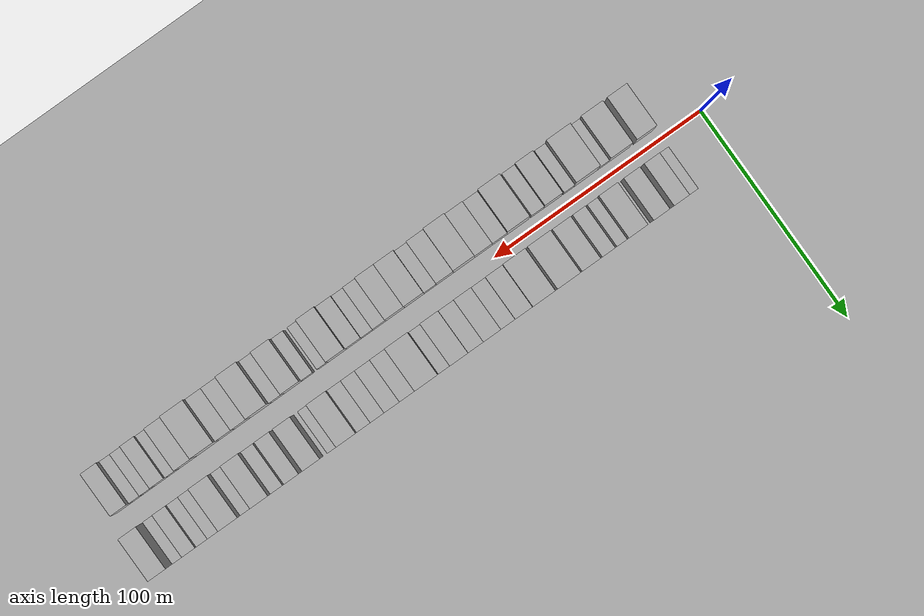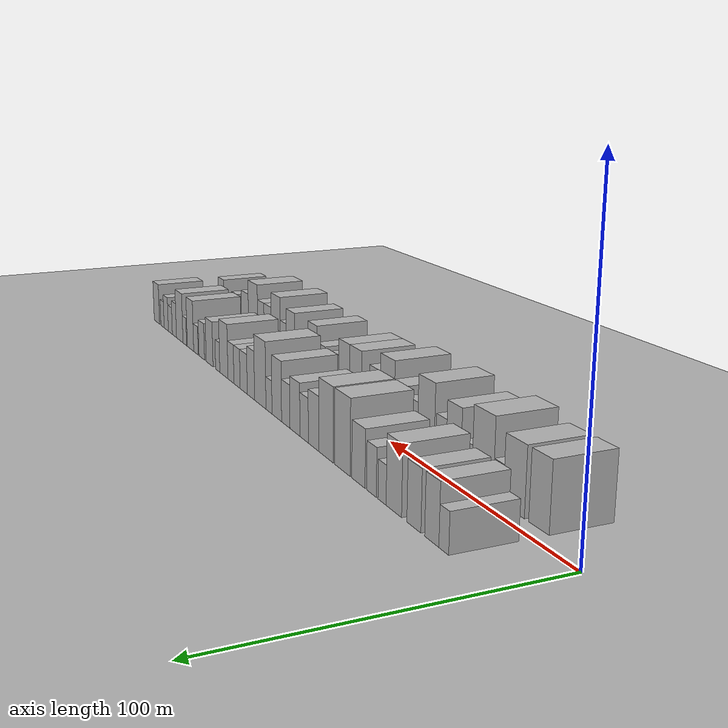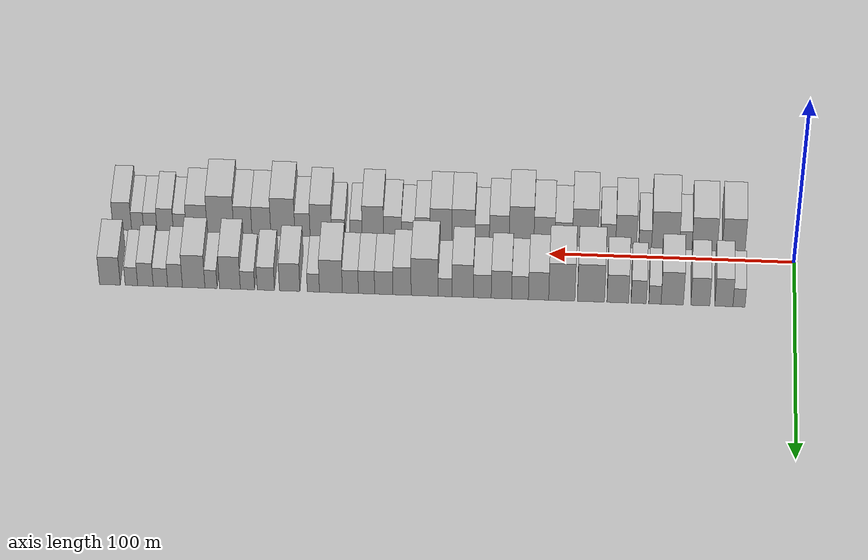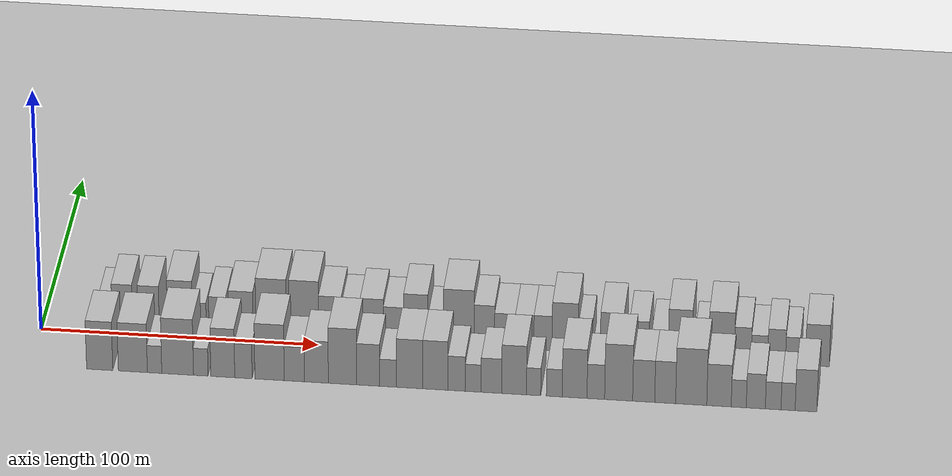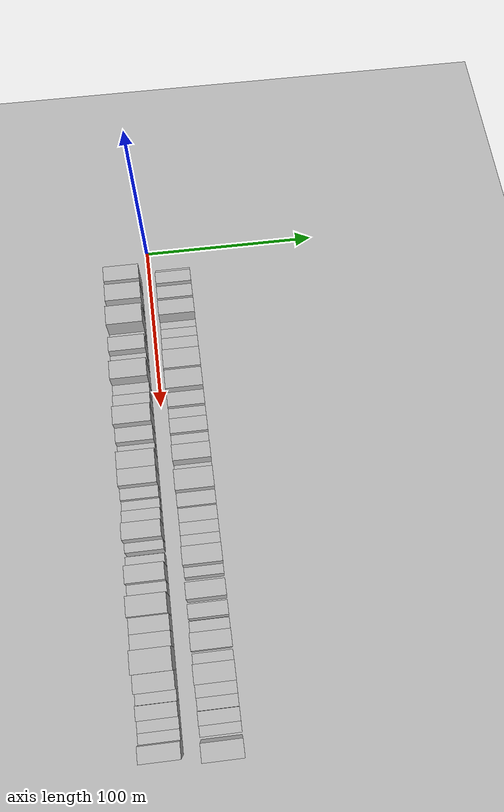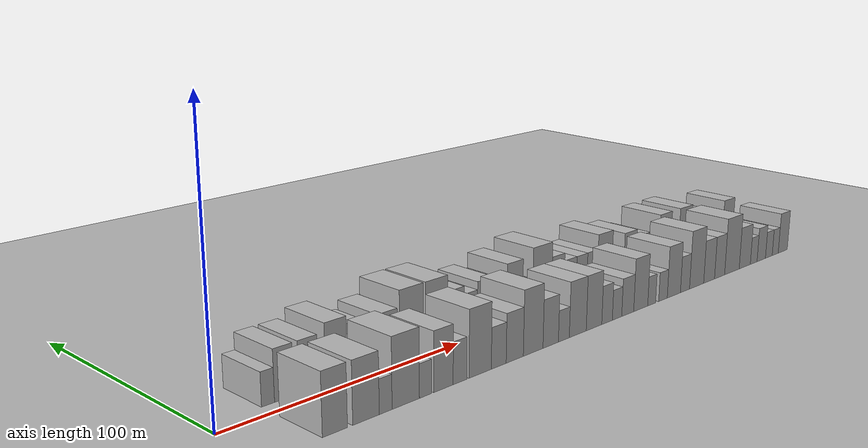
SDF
<?xml version="1.0" encoding="utf-8"?>

<sdf version="1.6">

   <world name="default">

      <gui fullscreen="0">

         <camera name="user_camera">

            <pose>-15 0 4.57585 0 0 0</pose>

            <view_controller>orbit</view_controller>

         </camera>

      </gui>

      <scene>

         <sky>

           <clouds>

             <speed>12</speed>

           </clouds>

         </sky>

         <ambient>0.4 0.4 0.4 1</ambient>

         <background>0.7 0.7 0.7 1</background>

         <shadows>1</shadows>

      </scene>

      <gravity>0 0 -9.8066</gravity>

      <magnetic_field>6e-06 2.3e-05 -4.2e-05</magnetic_field>

      <physics default="0" name="default_physics" type="ode">

         <ode>

            <solver>

               <type>quick</type>

               <iters>10</iters>

               <sor>1.0</sor>

               <use_dynamic_moi_rescaling>0</use_dynamic_moi_rescaling>

            </solver>

            <constraints>

               <cfm>0</cfm>

               <erp>0.2</erp>

               <contact_max_correcting_vel>100</contact_max_correcting_vel>

               <contact_surface_layer>0.001</contact_surface_layer>

            </constraints>

         </ode>

         <max_step_size>0.004</max_step_size>

         <real_time_factor>1</real_time_factor>

         <real_time_update_rate>250</real_time_update_rate>

      </physics>

      <light name="sun" type="directional">

         <cast_shadows>1</cast_shadows>

         <pose>0 0 10 0 0 0</pose>

         <diffuse>0.8 0.8 0.8 1</diffuse>

         <specular>0.2 0.2 0.2 1</specular>

         <attenuation>

            <range>1000</range>

            <constant>0.9</constant>

            <linear>0.01</linear>

            <quadratic>0.001</quadratic>

         </attenuation>

         <direction>-0.5 0.1 -0.9</direction>

      </light>

      <include>

         <name>ground_plane_1</name>

         <uri>model://HANNAS_ground_plane</uri>

         <pose>0 0 0  0 0 0</pose>

      </include>

      <include>

         <name>ground_plane_2</name>

         <uri>model://HANNAS_ground_plane</uri>

         <pose>100 0 0  0 0 0</pose>

      </include>

      <model name="building_1">

         <static>1</static>

         <pose frame="">22.4527 14.5000 0 0.000000 0.000000 1.570796</pose>

         <link name="link">

            <pose frame="">0 0 6.00 0 0 0</pose>

            <collision name="collision">

               <geometry>

                  <box>

                     <size>20.0000 4.9055 12.0000</size>

                  </box>

               </geometry>

               <max_contacts>10</max_contacts>

               <surface>

                  <contact>

                     <ode/>

                  </contact>

                  <bounce/>

                  <friction>

                     <torsional>

                        <ode/>

                     </torsional>

                     <ode/>

                  </friction>

               </surface>

            </collision>

            <visual name="visual">

               <cast_shadows>0</cast_shadows>

               <geometry>

                  <box>

                     <size>20.0000 4.9055 12.0000</size>

                  </box>

               </geometry>

               <material>

                  <script>

                     <uri>model://HANNAS_wall/materials/scripts</uri>

                     <uri>model://HANNAS_wall/materials/textures</uri>

                     <name>vrc/HANNAS_wall</name>

                  </script>

               </material>

            </visual>

            <self_collide>0</self_collide>

            <enable_wind>0</enable_wind>

            <kinematic>0</kinematic>

         </link>

      </model>

      <model name="building_2">

         <static>1</static>

         <pose frame="">28.5818 14.5000 0 0.000000 0.000000 1.570796</pose>

         <link name="link">

            <pose frame="">0 0 9.00 0 0 0</pose>

            <collision name="collision">

               <geometry>

                  <box>

                     <size>20.0000 7.3527 18.0000</size>

                  </box>

               </geometry>

               <max_contacts>10</max_contacts>

               <surface>

                  <contact>

                     <ode/>

                  </contact>

                  <bounce/>

                  <friction>

                     <torsional>

                        <ode/>

                     </torsional>

                     <ode/>

                  </friction>

               </surface>

            </collision>

            <visual name="visual">

               <cast_shadows>0</cast_shadows>

               <geometry>

                  <box>

                     <size>20.0000 7.3527 18.0000</size>

                  </box>

               </geometry>

               <material>

                  <script>

                     <uri>model://HANNAS_wall/materials/scripts</uri>

                     <uri>model://HANNAS_wall/materials/textures</uri>

                     <name>vrc/HANNAS_wall</name>

                  </script>

               </material>

            </visual>

            <self_collide>0</self_collide>

            <enable_wind>0</enable_wind>

            <kinematic>0</kinematic>

         </link>

      </model>

      <model name="building_3">

         <static>1</static>

         <pose frame="">38.1045 14.5000 0 0.000000 0.000000 1.570796</pose>

         <link name="link">

            <pose frame="">0 0 9.00 0 0 0</pose>

            <collision name="collision">

               <geometry>

                  <box>

                     <size>20.0000 7.6926 18.0000</size>

                  </box>

               </geometry>

               <max_contacts>10</max_contacts>

               <surface>

                  <contact>

                     <ode/>

                  </contact>

                  <bounce/>

                  <friction>

                     <torsional>

                        <ode/>

                     </torsional>

                     <ode/>

                  </friction>

               </surface>

            </collision>

            <visual name="visual">

               <cast_shadows>0</cast_shadows>

               <geometry>

                  <box>

                     <size>20.0000 7.6926 18.0000</size>

                  </box>

               </geometry>

               <material>

                  <script>

                     <uri>model://HANNAS_wall/materials/scripts</uri>

                     <uri>model://HANNAS_wall/materials/textures</uri>

                     <name>vrc/HANNAS_wall</name>

                  </script>

               </material>

            </visual>

            <self_collide>0</self_collide>

            <enable_wind>0</enable_wind>

            <kinematic>0</kinematic>

         </link>

      </model>

      <model name="building_4">

         <static>1</static>

         <pose frame="">49.4682 14.5000 0 0.000000 0.000000 1.570796</pose>

         <link name="link">

            <pose frame="">0 0 10.50 0 0 0</pose>

            <collision name="collision">

               <geometry>

                  <box>

                     <size>20.0000 9.0349 21.0000</size>

                  </box>

               </geometry>

               <max_contacts>10</max_contacts>

               <surface>

                  <contact>

                     <ode/>

                  </contact>

                  <bounce/>

                  <friction>

                     <torsional>

                        <ode/>

                     </torsional>

                     <ode/>

                  </friction>

               </surface>

            </collision>

            <visual name="visual">

               <cast_shadows>0</cast_shadows>

               <geometry>

                  <box>

                     <size>20.0000 9.0349 21.0000</size>

                  </box>

               </geometry>

               <material>

                  <script>

                     <uri>model://HANNAS_wall/materials/scripts</uri>

                     <uri>model://HANNAS_wall/materials/textures</uri>

                     <name>vrc/HANNAS_wall</name>

                  </script>

               </material>

            </visual>

            <self_collide>0</self_collide>

            <enable_wind>0</enable_wind>

            <kinematic>0</kinematic>

         </link>

      </model>

      <model name="building_5">

         <static>1</static>

         <pose frame="">56.4635 14.5000 0 0.000000 0.000000 1.570796</pose>

         <link name="link">

            <pose frame="">0 0 6.00 0 0 0</pose>

            <collision name="collision">

               <geometry>

                  <box>

                     <size>20.0000 4.9556 12.0000</size>

                  </box>

               </geometry>

               <max_contacts>10</max_contacts>

               <surface>

                  <contact>

                     <ode/>

                  </contact>

                  <bounce/>

                  <friction>

                     <torsional>

                        <ode/>

                     </torsional>

                     <ode/>

                  </friction>

               </surface>

            </collision>

            <visual name="visual">

               <cast_shadows>0</cast_shadows>

               <geometry>

                  <box>

                     <size>20.0000 4.9556 12.0000</size>

                  </box>

               </geometry>

               <material>

                  <script>

                     <uri>model://HANNAS_wall/materials/scripts</uri>

                     <uri>model://HANNAS_wall/materials/textures</uri>

                     <name>vrc/HANNAS_wall</name>

                  </script>

               </material>

            </visual>

            <self_collide>0</self_collide>

            <enable_wind>0</enable_wind>

            <kinematic>0</kinematic>

         </link>

      </model>

      <model name="building_6">

         <static>1</static>

         <pose frame="">63.0217 14.5000 0 0.000000 0.000000 1.570796</pose>

         <link name="link">

            <pose frame="">0 0 7.50 0 0 0</pose>

            <collision name="collision">

               <geometry>

                  <box>

                     <size>20.0000 6.1607 15.0000</size>

                  </box>

               </geometry>

               <max_contacts>10</max_contacts>

               <surface>

                  <contact>

                     <ode/>

                  </contact>

                  <bounce/>

                  <friction>

                     <torsional>

                        <ode/>

                     </torsional>

                     <ode/>

                  </friction>

               </surface>

            </collision>

            <visual name="visual">

               <cast_shadows>0</cast_shadows>

               <geometry>

                  <box>

                     <size>20.0000 6.1607 15.0000</size>

                  </box>

               </geometry>

               <material>

                  <script>

                     <uri>model://HANNAS_wall/materials/scripts</uri>

                     <uri>model://HANNAS_wall/materials/textures</uri>

                     <name>vrc/HANNAS_wall</name>

                  </script>

               </material>

            </visual>

            <self_collide>0</self_collide>

            <enable_wind>0</enable_wind>

            <kinematic>0</kinematic>

         </link>

      </model>

      <model name="building_7">

         <static>1</static>

         <pose frame="">71.4967 14.5000 0 0.000000 0.000000 1.570796</pose>

         <link name="link">

            <pose frame="">0 0 9.00 0 0 0</pose>

            <collision name="collision">

               <geometry>

                  <box>

                     <size>20.0000 8.7894 18.0000</size>

                  </box>

               </geometry>

               <max_contacts>10</max_contacts>

               <surface>

                  <contact>

                     <ode/>

                  </contact>

                  <bounce/>

                  <friction>

                     <torsional>

                        <ode/>

                     </torsional>

                     <ode/>

                  </friction>

               </surface>

            </collision>

            <visual name="visual">

               <cast_shadows>0</cast_shadows>

               <geometry>

                  <box>

                     <size>20.0000 8.7894 18.0000</size>

                  </box>

               </geometry>

               <material>

                  <script>

                     <uri>model://HANNAS_wall/materials/scripts</uri>

                     <uri>model://HANNAS_wall/materials/textures</uri>

                     <name>vrc/HANNAS_wall</name>

                  </script>

               </material>

            </visual>

            <self_collide>0</self_collide>

            <enable_wind>0</enable_wind>

            <kinematic>0</kinematic>

         </link>

      </model>

      <model name="building_8">

         <static>1</static>

         <pose frame="">82.3796 14.5000 0 0.000000 0.000000 1.570796</pose>

         <link name="link">

            <pose frame="">0 0 12.00 0 0 0</pose>

            <collision name="collision">

               <geometry>

                  <box>

                     <size>20.0000 10.9763 24.0000</size>

                  </box>

               </geometry>

               <max_contacts>10</max_contacts>

               <surface>

                  <contact>

                     <ode/>

                  </contact>

                  <bounce/>

                  <friction>

                     <torsional>

                        <ode/>

                     </torsional>

                     <ode/>

                  </friction>

               </surface>

            </collision>

            <visual name="visual">

               <cast_shadows>0</cast_shadows>

               <geometry>

                  <box>

                     <size>20.0000 10.9763 24.0000</size>

                  </box>

               </geometry>

               <material>

                  <script>

                     <uri>model://HANNAS_wall/materials/scripts</uri>

                     <uri>model://HANNAS_wall/materials/textures</uri>

                     <name>vrc/HANNAS_wall</name>

                  </script>

               </material>

            </visual>

            <self_collide>0</self_collide>

            <enable_wind>0</enable_wind>

            <kinematic>0</kinematic>

         </link>

      </model>

      <model name="building_9">

         <static>1</static>

         <pose frame="">94.1800 14.5000 0 0.000000 0.000000 1.570796</pose>

         <link name="link">

            <pose frame="">0 0 12.00 0 0 0</pose>

            <collision name="collision">

               <geometry>

                  <box>

                     <size>20.0000 10.6246 24.0000</size>

                  </box>

               </geometry>

               <max_contacts>10</max_contacts>

               <surface>

                  <contact>

                     <ode/>

                  </contact>

                  <bounce/>

                  <friction>

                     <torsional>

                        <ode/>

                     </torsional>

                     <ode/>

                  </friction>

               </surface>

            </collision>

            <visual name="visual">

               <cast_shadows>0</cast_shadows>

               <geometry>

                  <box>

                     <size>20.0000 10.6246 24.0000</size>

                  </box>

               </geometry>

               <material>

                  <script>

                     <uri>model://HANNAS_wall/materials/scripts</uri>

                     <uri>model://HANNAS_wall/materials/textures</uri>

                     <name>vrc/HANNAS_wall</name>

                  </script>

               </material>

            </visual>

            <self_collide>0</self_collide>

            <enable_wind>0</enable_wind>

            <kinematic>0</kinematic>

         </link>

      </model>

      <model name="building_10">

         <static>1</static>

         <pose frame="">103.5946 14.5000 0 0.000000 0.000000 1.570796</pose>

         <link name="link">

            <pose frame="">0 0 9.00 0 0 0</pose>

            <collision name="collision">

               <geometry>

                  <box>

                     <size>20.0000 8.2046 18.0000</size>

                  </box>

               </geometry>

               <max_contacts>10</max_contacts>

               <surface>

                  <contact>

                     <ode/>

                  </contact>

                  <bounce/>

                  <friction>

                     <torsional>

                        <ode/>

                     </torsional>

                     <ode/>

                  </friction>

               </surface>

            </collision>

            <visual name="visual">

               <cast_shadows>0</cast_shadows>

               <geometry>

                  <box>

                     <size>20.0000 8.2046 18.0000</size>

                  </box>

               </geometry>

               <material>

                  <script>

                     <uri>model://HANNAS_wall/materials/scripts</uri>

                     <uri>model://HANNAS_wall/materials/textures</uri>

                     <name>vrc/HANNAS_wall</name>

                  </script>

               </material>

            </visual>

            <self_collide>0</self_collide>

            <enable_wind>0</enable_wind>

            <kinematic>0</kinematic>

         </link>

      </model>

      <model name="building_11">

         <static>1</static>

         <pose frame="">111.0911 14.5000 0 0.000000 0.000000 1.570796</pose>

         <link name="link">

            <pose frame="">0 0 7.50 0 0 0</pose>

            <collision name="collision">

               <geometry>

                  <box>

                     <size>20.0000 6.7883 15.0000</size>

                  </box>

               </geometry>

               <max_contacts>10</max_contacts>

               <surface>

                  <contact>

                     <ode/>

                  </contact>

                  <bounce/>

                  <friction>

                     <torsional>

                        <ode/>

                     </torsional>

                     <ode/>

                  </friction>

               </surface>

            </collision>

            <visual name="visual">

               <cast_shadows>0</cast_shadows>

               <geometry>

                  <box>

                     <size>20.0000 6.7883 15.0000</size>

                  </box>

               </geometry>

               <material>

                  <script>

                     <uri>model://HANNAS_wall/materials/scripts</uri>

                     <uri>model://HANNAS_wall/materials/textures</uri>

                     <name>vrc/HANNAS_wall</name>

                  </script>

               </material>

            </visual>

            <self_collide>0</self_collide>

            <enable_wind>0</enable_wind>

            <kinematic>0</kinematic>

         </link>

      </model>

      <model name="building_12">

         <static>1</static>

         <pose frame="">118.6386 14.5000 0 0.000000 0.000000 1.570796</pose>

         <link name="link">

            <pose frame="">0 0 9.00 0 0 0</pose>

            <collision name="collision">

               <geometry>

                  <box>

                     <size>20.0000 8.3067 18.0000</size>

                  </box>

               </geometry>

               <max_contacts>10</max_contacts>

               <surface>

                  <contact>

                     <ode/>

                  </contact>

                  <bounce/>

                  <friction>

                     <torsional>

                        <ode/>

                     </torsional>

                     <ode/>

                  </friction>

               </surface>

            </collision>

            <visual name="visual">

               <cast_shadows>0</cast_shadows>

               <geometry>

                  <box>

                     <size>20.0000 8.3067 18.0000</size>

                  </box>

               </geometry>

               <material>

                  <script>

                     <uri>model://HANNAS_wall/materials/scripts</uri>

                     <uri>model://HANNAS_wall/materials/textures</uri>

                     <name>vrc/HANNAS_wall</name>

                  </script>

               </material>

            </visual>

            <self_collide>0</self_collide>

            <enable_wind>0</enable_wind>

            <kinematic>0</kinematic>

         </link>

      </model>

      <model name="building_13">

         <static>1</static>

         <pose frame="">126.4335 14.5000 0 0.000000 0.000000 1.570796</pose>

         <link name="link">

            <pose frame="">0 0 7.50 0 0 0</pose>

            <collision name="collision">

               <geometry>

                  <box>

                     <size>20.0000 7.2832 15.0000</size>

                  </box>

               </geometry>

               <max_contacts>10</max_contacts>

               <surface>

                  <contact>

                     <ode/>

                  </contact>

                  <bounce/>

                  <friction>

                     <torsional>

                        <ode/>

                     </torsional>

                     <ode/>

                  </friction>

               </surface>

            </collision>

            <visual name="visual">

               <cast_shadows>0</cast_shadows>

               <geometry>

                  <box>

                     <size>20.0000 7.2832 15.0000</size>

                  </box>

               </geometry>

               <material>

                  <script>

                     <uri>model://HANNAS_wall/materials/scripts</uri>

                     <uri>model://HANNAS_wall/materials/textures</uri>

                     <name>vrc/HANNAS_wall</name>

                  </script>

               </material>

            </visual>

            <self_collide>0</self_collide>

            <enable_wind>0</enable_wind>

            <kinematic>0</kinematic>

         </link>

      </model>

      <model name="building_14">

         <static>1</static>

         <pose frame="">134.3953 14.5000 0 0.000000 0.000000 1.570796</pose>

         <link name="link">

            <pose frame="">0 0 10.50 0 0 0</pose>

            <collision name="collision">

               <geometry>

                  <box>

                     <size>20.0000 8.6404 21.0000</size>

                  </box>

               </geometry>

               <max_contacts>10</max_contacts>

               <surface>

                  <contact>

                     <ode/>

                  </contact>

                  <bounce/>

                  <friction>

                     <torsional>

                        <ode/>

                     </torsional>

                     <ode/>

                  </friction>

               </surface>

            </collision>

            <visual name="visual">

               <cast_shadows>0</cast_shadows>

               <geometry>

                  <box>

                     <size>20.0000 8.6404 21.0000</size>

                  </box>

               </geometry>

               <material>

                  <script>

                     <uri>model://HANNAS_wall/materials/scripts</uri>

                     <uri>model://HANNAS_wall/materials/textures</uri>

                     <name>vrc/HANNAS_wall</name>

                  </script>

               </material>

            </visual>

            <self_collide>0</self_collide>

            <enable_wind>0</enable_wind>

            <kinematic>0</kinematic>

         </link>

      </model>

      <model name="building_15">

         <static>1</static>

         <pose frame="">141.5295 14.5000 0 0.000000 0.000000 1.570796</pose>

         <link name="link">

            <pose frame="">0 0 6.00 0 0 0</pose>

            <collision name="collision">

               <geometry>

                  <box>

                     <size>20.0000 5.6282 12.0000</size>

                  </box>

               </geometry>

               <max_contacts>10</max_contacts>

               <surface>

                  <contact>

                     <ode/>

                  </contact>

                  <bounce/>

                  <friction>

                     <torsional>

                        <ode/>

                     </torsional>

                     <ode/>

                  </friction>

               </surface>

            </collision>

            <visual name="visual">

               <cast_shadows>0</cast_shadows>

               <geometry>

                  <box>

                     <size>20.0000 5.6282 12.0000</size>

                  </box>

               </geometry>

               <material>

                  <script>

                     <uri>model://HANNAS_wall/materials/scripts</uri>

                     <uri>model://HANNAS_wall/materials/textures</uri>

                     <name>vrc/HANNAS_wall</name>

                  </script>

               </material>

            </visual>

            <self_collide>0</self_collide>

            <enable_wind>0</enable_wind>

            <kinematic>0</kinematic>

         </link>

      </model>

      <model name="building_16">

         <static>1</static>

         <pose frame="">149.8142 14.5000 0 0.000000 0.000000 1.570796</pose>

         <link name="link">

            <pose frame="">0 0 12.00 0 0 0</pose>

            <collision name="collision">

               <geometry>

                  <box>

                     <size>20.0000 10.9413 24.0000</size>

                  </box>

               </geometry>

               <max_contacts>10</max_contacts>

               <surface>

                  <contact>

                     <ode/>

                  </contact>

                  <bounce/>

                  <friction>

                     <torsional>

                        <ode/>

                     </torsional>

                     <ode/>

                  </friction>

               </surface>

            </collision>

            <visual name="visual">

               <cast_shadows>0</cast_shadows>

               <geometry>

                  <box>

                     <size>20.0000 10.9413 24.0000</size>

                  </box>

               </geometry>

               <material>

                  <script>

                     <uri>model://HANNAS_wall/materials/scripts</uri>

                     <uri>model://HANNAS_wall/materials/textures</uri>

                     <name>vrc/HANNAS_wall</name>

                  </script>

               </material>

            </visual>

            <self_collide>0</self_collide>

            <enable_wind>0</enable_wind>

            <kinematic>0</kinematic>

         </link>

      </model>

      <model name="building_17">

         <static>1</static>

         <pose frame="">158.9749 14.5000 0 0.000000 0.000000 1.570796</pose>

         <link name="link">

            <pose frame="">0 0 9.00 0 0 0</pose>

            <collision name="collision">

               <geometry>

                  <box>

                     <size>20.0000 7.3801 18.0000</size>

                  </box>

               </geometry>

               <max_contacts>10</max_contacts>

               <surface>

                  <contact>

                     <ode/>

                  </contact>

                  <bounce/>

                  <friction>

                     <torsional>

                        <ode/>

                     </torsional>

                     <ode/>

                  </friction>

               </surface>

            </collision>

            <visual name="visual">

               <cast_shadows>0</cast_shadows>

               <geometry>

                  <box>

                     <size>20.0000 7.3801 18.0000</size>

                  </box>

               </geometry>

               <material>

                  <script>

                     <uri>model://HANNAS_wall/materials/scripts</uri>

                     <uri>model://HANNAS_wall/materials/textures</uri>

                     <name>vrc/HANNAS_wall</name>

                  </script>

               </material>

            </visual>

            <self_collide>0</self_collide>

            <enable_wind>0</enable_wind>

            <kinematic>0</kinematic>

         </link>

      </model>

      <model name="building_18">

         <static>1</static>

         <pose frame="">166.3791 14.5000 0 0.000000 0.000000 1.570796</pose>

         <link name="link">

            <pose frame="">0 0 7.50 0 0 0</pose>

            <collision name="collision">

               <geometry>

                  <box>

                     <size>20.0000 7.4284 15.0000</size>

                  </box>

               </geometry>

               <max_contacts>10</max_contacts>

               <surface>

                  <contact>

                     <ode/>

                  </contact>

                  <bounce/>

                  <friction>

                     <torsional>

                        <ode/>

                     </torsional>

                     <ode/>

                  </friction>

               </surface>

            </collision>

            <visual name="visual">

               <cast_shadows>0</cast_shadows>

               <geometry>

                  <box>

                     <size>20.0000 7.4284 15.0000</size>

                  </box>

               </geometry>

               <material>

                  <script>

                     <uri>model://HANNAS_wall/materials/scripts</uri>

                     <uri>model://HANNAS_wall/materials/textures</uri>

                     <name>vrc/HANNAS_wall</name>

                  </script>

               </material>

            </visual>

            <self_collide>0</self_collide>

            <enable_wind>0</enable_wind>

            <kinematic>0</kinematic>

         </link>

      </model>

      <model name="building_19">

         <static>1</static>

         <pose frame="">173.3979 14.5000 0 0.000000 0.000000 1.570796</pose>

         <link name="link">

            <pose frame="">0 0 7.50 0 0 0</pose>

            <collision name="collision">

               <geometry>

                  <box>

                     <size>20.0000 6.6092 15.0000</size>

                  </box>

               </geometry>

               <max_contacts>10</max_contacts>

               <surface>

                  <contact>

                     <ode/>

                  </contact>

                  <bounce/>

                  <friction>

                     <torsional>

                        <ode/>

                     </torsional>

                     <ode/>

                  </friction>

               </surface>

            </collision>

            <visual name="visual">

               <cast_shadows>0</cast_shadows>

               <geometry>

                  <box>

                     <size>20.0000 6.6092 15.0000</size>

                  </box>

               </geometry>

               <material>

                  <script>

                     <uri>model://HANNAS_wall/materials/scripts</uri>

                     <uri>model://HANNAS_wall/materials/textures</uri>

                     <name>vrc/HANNAS_wall</name>

                  </script>

               </material>

            </visual>

            <self_collide>0</self_collide>

            <enable_wind>0</enable_wind>

            <kinematic>0</kinematic>

         </link>

      </model>

      <model name="building_20">

         <static>1</static>

         <pose frame="">179.9726 14.5000 0 0.000000 0.000000 1.570796</pose>

         <link name="link">

            <pose frame="">0 0 7.50 0 0 0</pose>

            <collision name="collision">

               <geometry>

                  <box>

                     <size>20.0000 6.5402 15.0000</size>

                  </box>

               </geometry>

               <max_contacts>10</max_contacts>

               <surface>

                  <contact>

                     <ode/>

                  </contact>

                  <bounce/>

                  <friction>

                     <torsional>

                        <ode/>

                     </torsional>

                     <ode/>

                  </friction>

               </surface>

            </collision>

            <visual name="visual">

               <cast_shadows>0</cast_shadows>

               <geometry>

                  <box>

                     <size>20.0000 6.5402 15.0000</size>

                  </box>

               </geometry>

               <material>

                  <script>

                     <uri>model://HANNAS_wall/materials/scripts</uri>

                     <uri>model://HANNAS_wall/materials/textures</uri>

                     <name>vrc/HANNAS_wall</name>

                  </script>

               </material>

            </visual>

            <self_collide>0</self_collide>

            <enable_wind>0</enable_wind>

            <kinematic>0</kinematic>

         </link>

      </model>

      <model name="building_21">

         <static>1</static>

         <pose frame="">187.8923 14.5000 0 0.000000 0.000000 1.570796</pose>

         <link name="link">

            <pose frame="">0 0 10.50 0 0 0</pose>

            <collision name="collision">

               <geometry>

                  <box>

                     <size>20.0000 9.2992 21.0000</size>

                  </box>

               </geometry>

               <max_contacts>10</max_contacts>

               <surface>

                  <contact>

                     <ode/>

                  </contact>

                  <bounce/>

                  <friction>

                     <torsional>

                        <ode/>

                     </torsional>

                     <ode/>

                  </friction>

               </surface>

            </collision>

            <visual name="visual">

               <cast_shadows>0</cast_shadows>

               <geometry>

                  <box>

                     <size>20.0000 9.2992 21.0000</size>

                  </box>

               </geometry>

               <material>

                  <script>

                     <uri>model://HANNAS_wall/materials/scripts</uri>

                     <uri>model://HANNAS_wall/materials/textures</uri>

                     <name>vrc/HANNAS_wall</name>

                  </script>

               </material>

            </visual>

            <self_collide>0</self_collide>

            <enable_wind>0</enable_wind>

            <kinematic>0</kinematic>

         </link>

      </model>

      <model name="building_22">

         <static>1</static>

         <pose frame="">195.0158 14.5000 0 0.000000 0.000000 1.570796</pose>

         <link name="link">

            <pose frame="">0 0 6.00 0 0 0</pose>

            <collision name="collision">

               <geometry>

                  <box>

                     <size>20.0000 4.9476 12.0000</size>

                  </box>

               </geometry>

               <max_contacts>10</max_contacts>

               <surface>

                  <contact>

                     <ode/>

                  </contact>

                  <bounce/>

                  <friction>

                     <torsional>

                        <ode/>

                     </torsional>

                     <ode/>

                  </friction>

               </surface>

            </collision>

            <visual name="visual">

               <cast_shadows>0</cast_shadows>

               <geometry>

                  <box>

                     <size>20.0000 4.9476 12.0000</size>

                  </box>

               </geometry>

               <material>

                  <script>

                     <uri>model://HANNAS_wall/materials/scripts</uri>

                     <uri>model://HANNAS_wall/materials/textures</uri>

                     <name>vrc/HANNAS_wall</name>

                  </script>

               </material>

            </visual>

            <self_collide>0</self_collide>

            <enable_wind>0</enable_wind>

            <kinematic>0</kinematic>

         </link>

      </model>

      <model name="building_23">

         <static>1</static>

         <pose frame="">204.6551 14.5000 0 0.000000 0.000000 1.570796</pose>

         <link name="link">

            <pose frame="">0 0 9.00 0 0 0</pose>

            <collision name="collision">

               <geometry>

                  <box>

                     <size>20.0000 8.3310 18.0000</size>

                  </box>

               </geometry>

               <max_contacts>10</max_contacts>

               <surface>

                  <contact>

                     <ode/>

                  </contact>

                  <bounce/>

                  <friction>

                     <torsional>

                        <ode/>

                     </torsional>

                     <ode/>

                  </friction>

               </surface>

            </collision>

            <visual name="visual">

               <cast_shadows>0</cast_shadows>

               <geometry>

                  <box>

                     <size>20.0000 8.3310 18.0000</size>

                  </box>

               </geometry>

               <material>

                  <script>

                     <uri>model://HANNAS_wall/materials/scripts</uri>

                     <uri>model://HANNAS_wall/materials/textures</uri>

                     <name>vrc/HANNAS_wall</name>

                  </script>

               </material>

            </visual>

            <self_collide>0</self_collide>

            <enable_wind>0</enable_wind>

            <kinematic>0</kinematic>

         </link>

      </model>

      <model name="building_24">

         <static>1</static>

         <pose frame="">214.3445 14.5000 0 0.000000 0.000000 1.570796</pose>

         <link name="link">

            <pose frame="">0 0 7.50 0 0 0</pose>

            <collision name="collision">

               <geometry>

                  <box>

                     <size>20.0000 7.0478 15.0000</size>

                  </box>

               </geometry>

               <max_contacts>10</max_contacts>

               <surface>

                  <contact>

                     <ode/>

                  </contact>

                  <bounce/>

                  <friction>

                     <torsional>

                        <ode/>

                     </torsional>

                     <ode/>

                  </friction>

               </surface>

            </collision>

            <visual name="visual">

               <cast_shadows>0</cast_shadows>

               <geometry>

                  <box>

                     <size>20.0000 7.0478 15.0000</size>

                  </box>

               </geometry>

               <material>

                  <script>

                     <uri>model://HANNAS_wall/materials/scripts</uri>

                     <uri>model://HANNAS_wall/materials/textures</uri>

                     <name>vrc/HANNAS_wall</name>

                  </script>

               </material>

            </visual>

            <self_collide>0</self_collide>

            <enable_wind>0</enable_wind>

            <kinematic>0</kinematic>

         </link>

      </model>

      <model name="building_25">

         <static>1</static>

         <pose frame="">221.7925 14.5000 0 0.000000 0.000000 1.570796</pose>

         <link name="link">

            <pose frame="">0 0 6.00 0 0 0</pose>

            <collision name="collision">

               <geometry>

                  <box>

                     <size>20.0000 5.8482 12.0000</size>

                  </box>

               </geometry>

               <max_contacts>10</max_contacts>

               <surface>

                  <contact>

                     <ode/>

                  </contact>

                  <bounce/>

                  <friction>

                     <torsional>

                        <ode/>

                     </torsional>

                     <ode/>

                  </friction>

               </surface>

            </collision>

            <visual name="visual">

               <cast_shadows>0</cast_shadows>

               <geometry>

                  <box>

                     <size>20.0000 5.8482 12.0000</size>

                  </box>

               </geometry>

               <material>

                  <script>

                     <uri>model://HANNAS_wall/materials/scripts</uri>

                     <uri>model://HANNAS_wall/materials/textures</uri>

                     <name>vrc/HANNAS_wall</name>

                  </script>

               </material>

            </visual>

            <self_collide>0</self_collide>

            <enable_wind>0</enable_wind>

            <kinematic>0</kinematic>

         </link>

      </model>

      <model name="building_26">

         <static>1</static>

         <pose frame="">228.9413 14.5000 0 0.000000 0.000000 1.570796</pose>

         <link name="link">

            <pose frame="">0 0 10.50 0 0 0</pose>

            <collision name="collision">

               <geometry>

                  <box>

                     <size>20.0000 8.4494 21.0000</size>

                  </box>

               </geometry>

               <max_contacts>10</max_contacts>

               <surface>

                  <contact>

                     <ode/>

                  </contact>

                  <bounce/>

                  <friction>

                     <torsional>

                        <ode/>

                     </torsional>

                     <ode/>

                  </friction>

               </surface>

            </collision>

            <visual name="visual">

               <cast_shadows>0</cast_shadows>

               <geometry>

                  <box>

                     <size>20.0000 8.4494 21.0000</size>

                  </box>

               </geometry>

               <material>

                  <script>

                     <uri>model://HANNAS_wall/materials/scripts</uri>

                     <uri>model://HANNAS_wall/materials/textures</uri>

                     <name>vrc/HANNAS_wall</name>

                  </script>

               </material>

            </visual>

            <self_collide>0</self_collide>

            <enable_wind>0</enable_wind>

            <kinematic>0</kinematic>

         </link>

      </model>

      <model name="building_27">

         <static>1</static>

         <pose frame="">236.6416 14.5000 0 0.000000 0.000000 1.570796</pose>

         <link name="link">

            <pose frame="">0 0 6.00 0 0 0</pose>

            <collision name="collision">

               <geometry>

                  <box>

                     <size>20.0000 4.9512 12.0000</size>

                  </box>

               </geometry>

               <max_contacts>10</max_contacts>

               <surface>

                  <contact>

                     <ode/>

                  </contact>

                  <bounce/>

                  <friction>

                     <torsional>

                        <ode/>

                     </torsional>

                     <ode/>

                  </friction>

               </surface>

            </collision>

            <visual name="visual">

               <cast_shadows>0</cast_shadows>

               <geometry>

                  <box>

                     <size>20.0000 4.9512 12.0000</size>

                  </box>

               </geometry>

               <material>

                  <script>

                     <uri>model://HANNAS_wall/materials/scripts</uri>

                     <uri>model://HANNAS_wall/materials/textures</uri>

                     <name>vrc/HANNAS_wall</name>

                  </script>

               </material>

            </visual>

            <self_collide>0</self_collide>

            <enable_wind>0</enable_wind>

            <kinematic>0</kinematic>

         </link>

      </model>

      <model name="building_28">

         <static>1</static>

         <pose frame="">243.6999 14.5000 0 0.000000 0.000000 1.570796</pose>

         <link name="link">

            <pose frame="">0 0 10.50 0 0 0</pose>

            <collision name="collision">

               <geometry>

                  <box>

                     <size>20.0000 9.1655 21.0000</size>

                  </box>

               </geometry>

               <max_contacts>10</max_contacts>

               <surface>

                  <contact>

                     <ode/>

                  </contact>

                  <bounce/>

                  <friction>

                     <torsional>

                        <ode/>

                     </torsional>

                     <ode/>

                  </friction>

               </surface>

            </collision>

            <visual name="visual">

               <cast_shadows>0</cast_shadows>

               <geometry>

                  <box>

                     <size>20.0000 9.1655 21.0000</size>

                  </box>

               </geometry>

               <material>

                  <script>

                     <uri>model://HANNAS_wall/materials/scripts</uri>

                     <uri>model://HANNAS_wall/materials/textures</uri>

                     <name>vrc/HANNAS_wall</name>

                  </script>

               </material>

            </visual>

            <self_collide>0</self_collide>

            <enable_wind>0</enable_wind>

            <kinematic>0</kinematic>

         </link>

      </model>

      <model name="building_29">

         <static>1</static>

         <pose frame="">251.2862 14.5000 0 0.000000 0.000000 1.570796</pose>

         <link name="link">

            <pose frame="">0 0 7.50 0 0 0</pose>

            <collision name="collision">

               <geometry>

                  <box>

                     <size>20.0000 6.0071 15.0000</size>

                  </box>

               </geometry>

               <max_contacts>10</max_contacts>

               <surface>

                  <contact>

                     <ode/>

                  </contact>

                  <bounce/>

                  <friction>

                     <torsional>

                        <ode/>

                     </torsional>

                     <ode/>

                  </friction>

               </surface>

            </collision>

            <visual name="visual">

               <cast_shadows>0</cast_shadows>

               <geometry>

                  <box>

                     <size>20.0000 6.0071 15.0000</size>

                  </box>

               </geometry>

               <material>

                  <script>

                     <uri>model://HANNAS_wall/materials/scripts</uri>

                     <uri>model://HANNAS_wall/materials/textures</uri>

                     <name>vrc/HANNAS_wall</name>

                  </script>

               </material>

            </visual>

            <self_collide>0</self_collide>

            <enable_wind>0</enable_wind>

            <kinematic>0</kinematic>

         </link>

      </model>

      <model name="building_30">

         <static>1</static>

         <pose frame="">257.2351 14.5000 0 0.000000 0.000000 1.570796</pose>

         <link name="link">

            <pose frame="">0 0 6.00 0 0 0</pose>

            <collision name="collision">

               <geometry>

                  <box>

                     <size>20.0000 5.8907 12.0000</size>

                  </box>

               </geometry>

               <max_contacts>10</max_contacts>

               <surface>

                  <contact>

                     <ode/>

                  </contact>

                  <bounce/>

                  <friction>

                     <torsional>

                        <ode/>

                     </torsional>

                     <ode/>

                  </friction>

               </surface>

            </collision>

            <visual name="visual">

               <cast_shadows>0</cast_shadows>

               <geometry>

                  <box>

                     <size>20.0000 5.8907 12.0000</size>

                  </box>

               </geometry>

               <material>

                  <script>

                     <uri>model://HANNAS_wall/materials/scripts</uri>

                     <uri>model://HANNAS_wall/materials/textures</uri>

                     <name>vrc/HANNAS_wall</name>

                  </script>

               </material>

            </visual>

            <self_collide>0</self_collide>

            <enable_wind>0</enable_wind>

            <kinematic>0</kinematic>

         </link>

      </model>

      <model name="building_31">

         <static>1</static>

         <pose frame="">263.3478 14.5000 0 0.000000 0.000000 1.570796</pose>

         <link name="link">

            <pose frame="">0 0 7.50 0 0 0</pose>

            <collision name="collision">

               <geometry>

                  <box>

                     <size>20.0000 6.3346 15.0000</size>

                  </box>

               </geometry>

               <max_contacts>10</max_contacts>

               <surface>

                  <contact>

                     <ode/>

                  </contact>

                  <bounce/>

                  <friction>

                     <torsional>

                        <ode/>

                     </torsional>

                     <ode/>

                  </friction>

               </surface>

            </collision>

            <visual name="visual">

               <cast_shadows>0</cast_shadows>

               <geometry>

                  <box>

                     <size>20.0000 6.3346 15.0000</size>

                  </box>

               </geometry>

               <material>

                  <script>

                     <uri>model://HANNAS_wall/materials/scripts</uri>

                     <uri>model://HANNAS_wall/materials/textures</uri>

                     <name>vrc/HANNAS_wall</name>

                  </script>

               </material>

            </visual>

            <self_collide>0</self_collide>

            <enable_wind>0</enable_wind>

            <kinematic>0</kinematic>

         </link>

      </model>

      <model name="building_32">

         <static>1</static>

         <pose frame="">269.0631 14.5000 0 0.000000 0.000000 1.570796</pose>

         <link name="link">

            <pose frame="">0 0 6.00 0 0 0</pose>

            <collision name="collision">

               <geometry>

                  <box>

                     <size>20.0000 5.0959 12.0000</size>

                  </box>

               </geometry>

               <max_contacts>10</max_contacts>

               <surface>

                  <contact>

                     <ode/>

                  </contact>

                  <bounce/>

                  <friction>

                     <torsional>

                        <ode/>

                     </torsional>

                     <ode/>

                  </friction>

               </surface>

            </collision>

            <visual name="visual">

               <cast_shadows>0</cast_shadows>

               <geometry>

                  <box>

                     <size>20.0000 5.0959 12.0000</size>

                  </box>

               </geometry>

               <material>

                  <script>

                     <uri>model://HANNAS_wall/materials/scripts</uri>

                     <uri>model://HANNAS_wall/materials/textures</uri>

                     <name>vrc/HANNAS_wall</name>

                  </script>

               </material>

            </visual>

            <self_collide>0</self_collide>

            <enable_wind>0</enable_wind>

            <kinematic>0</kinematic>

         </link>

      </model>

      <model name="building_33">

         <static>1</static>

         <pose frame="">277.8406 14.5000 0 0.000000 0.000000 1.570796</pose>

         <link name="link">

            <pose frame="">0 0 9.00 0 0 0</pose>

            <collision name="collision">

               <geometry>

                  <box>

                     <size>20.0000 8.4593 18.0000</size>

                  </box>

               </geometry>

               <max_contacts>10</max_contacts>

               <surface>

                  <contact>

                     <ode/>

                  </contact>

                  <bounce/>

                  <friction>

                     <torsional>

                        <ode/>

                     </torsional>

                     <ode/>

                  </friction>

               </surface>

            </collision>

            <visual name="visual">

               <cast_shadows>0</cast_shadows>

               <geometry>

                  <box>

                     <size>20.0000 8.4593 18.0000</size>

                  </box>

               </geometry>

               <material>

                  <script>

                     <uri>model://HANNAS_wall/materials/scripts</uri>

                     <uri>model://HANNAS_wall/materials/textures</uri>

                     <name>vrc/HANNAS_wall</name>

                  </script>

               </material>

            </visual>

            <self_collide>0</self_collide>

            <enable_wind>0</enable_wind>

            <kinematic>0</kinematic>

         </link>

      </model>

      <model name="building_34">

         <static>1</static>

         <pose frame="">24.6891 -14.5000 0 0.000000 0.000000 1.570796</pose>

         <link name="link">

            <pose frame="">0 0 10.50 0 0 0</pose>

            <collision name="collision">

               <geometry>

                  <box>

                     <size>20.0000 9.3783 21.0000</size>

                  </box>

               </geometry>

               <max_contacts>10</max_contacts>

               <surface>

                  <contact>

                     <ode/>

                  </contact>

                  <bounce/>

                  <friction>

                     <torsional>

                        <ode/>

                     </torsional>

                     <ode/>

                  </friction>

               </surface>

            </collision>

            <visual name="visual">

               <cast_shadows>0</cast_shadows>

               <geometry>

                  <box>

                     <size>20.0000 9.3783 21.0000</size>

                  </box>

               </geometry>

               <material>

                  <script>

                     <uri>model://HANNAS_wall/materials/scripts</uri>

                     <uri>model://HANNAS_wall/materials/textures</uri>

                     <name>vrc/HANNAS_wall</name>

                  </script>

               </material>

            </visual>

            <self_collide>0</self_collide>

            <enable_wind>0</enable_wind>

            <kinematic>0</kinematic>

         </link>

      </model>

      <model name="building_35">

         <static>1</static>

         <pose frame="">36.5722 -14.5000 0 0.000000 0.000000 1.570796</pose>

         <link name="link">

            <pose frame="">0 0 10.50 0 0 0</pose>

            <collision name="collision">

               <geometry>

                  <box>

                     <size>20.0000 10.3879 21.0000</size>

                  </box>

               </geometry>

               <max_contacts>10</max_contacts>

               <surface>

                  <contact>

                     <ode/>

                  </contact>

                  <bounce/>

                  <friction>

                     <torsional>

                        <ode/>

                     </torsional>

                     <ode/>

                  </friction>

               </surface>

            </collision>

            <visual name="visual">

               <cast_shadows>0</cast_shadows>

               <geometry>

                  <box>

                     <size>20.0000 10.3879 21.0000</size>

                  </box>

               </geometry>

               <material>

                  <script>

                     <uri>model://HANNAS_wall/materials/scripts</uri>

                     <uri>model://HANNAS_wall/materials/textures</uri>

                     <name>vrc/HANNAS_wall</name>

                  </script>

               </material>

            </visual>

            <self_collide>0</self_collide>

            <enable_wind>0</enable_wind>

            <kinematic>0</kinematic>

         </link>

      </model>

      <model name="building_36">

         <static>1</static>

         <pose frame="">44.3453 -14.5000 0 0.000000 0.000000 1.570796</pose>

         <link name="link">

            <pose frame="">0 0 6.00 0 0 0</pose>

            <collision name="collision">

               <geometry>

                  <box>

                     <size>20.0000 5.1583 12.0000</size>

                  </box>

               </geometry>

               <max_contacts>10</max_contacts>

               <surface>

                  <contact>

                     <ode/>

                  </contact>

                  <bounce/>

                  <friction>

                     <torsional>

                        <ode/>

                     </torsional>

                     <ode/>

                  </friction>

               </surface>

            </collision>

            <visual name="visual">

               <cast_shadows>0</cast_shadows>

               <geometry>

                  <box>

                     <size>20.0000 5.1583 12.0000</size>

                  </box>

               </geometry>

               <material>

                  <script>

                     <uri>model://HANNAS_wall/materials/scripts</uri>

                     <uri>model://HANNAS_wall/materials/textures</uri>

                     <name>vrc/HANNAS_wall</name>

                  </script>

               </material>

            </visual>

            <self_collide>0</self_collide>

            <enable_wind>0</enable_wind>

            <kinematic>0</kinematic>

         </link>

      </model>

      <model name="building_37">

         <static>1</static>

         <pose frame="">52.6037 -14.5000 0 0.000000 0.000000 1.570796</pose>

         <link name="link">

            <pose frame="">0 0 12.00 0 0 0</pose>

            <collision name="collision">

               <geometry>

                  <box>

                     <size>20.0000 11.3585 24.0000</size>

                  </box>

               </geometry>

               <max_contacts>10</max_contacts>

               <surface>

                  <contact>

                     <ode/>

                  </contact>

                  <bounce/>

                  <friction>

                     <torsional>

                        <ode/>

                     </torsional>

                     <ode/>

                  </friction>

               </surface>

            </collision>

            <visual name="visual">

               <cast_shadows>0</cast_shadows>

               <geometry>

                  <box>

                     <size>20.0000 11.3585 24.0000</size>

                  </box>

               </geometry>

               <material>

                  <script>

                     <uri>model://HANNAS_wall/materials/scripts</uri>

                     <uri>model://HANNAS_wall/materials/textures</uri>

                     <name>vrc/HANNAS_wall</name>

                  </script>

               </material>

            </visual>

            <self_collide>0</self_collide>

            <enable_wind>0</enable_wind>

            <kinematic>0</kinematic>

         </link>

      </model>

      <model name="building_38">

         <static>1</static>

         <pose frame="">60.8786 -14.5000 0 0.000000 0.000000 1.570796</pose>

         <link name="link">

            <pose frame="">0 0 6.00 0 0 0</pose>

            <collision name="collision">

               <geometry>

                  <box>

                     <size>20.0000 5.1912 12.0000</size>

                  </box>

               </geometry>

               <max_contacts>10</max_contacts>

               <surface>

                  <contact>

                     <ode/>

                  </contact>

                  <bounce/>

                  <friction>

                     <torsional>

                        <ode/>

                     </torsional>

                     <ode/>

                  </friction>

               </surface>

            </collision>

            <visual name="visual">

               <cast_shadows>0</cast_shadows>

               <geometry>

                  <box>

                     <size>20.0000 5.1912 12.0000</size>

                  </box>

               </geometry>

               <material>

                  <script>

                     <uri>model://HANNAS_wall/materials/scripts</uri>

                     <uri>model://HANNAS_wall/materials/textures</uri>

                     <name>vrc/HANNAS_wall</name>

                  </script>

               </material>

            </visual>

            <self_collide>0</self_collide>

            <enable_wind>0</enable_wind>

            <kinematic>0</kinematic>

         </link>

      </model>

      <model name="building_39">

         <static>1</static>

         <pose frame="">68.7389 -14.5000 0 0.000000 0.000000 1.570796</pose>

         <link name="link">

            <pose frame="">0 0 10.50 0 0 0</pose>

            <collision name="collision">

               <geometry>

                  <box>

                     <size>20.0000 8.5294 21.0000</size>

                  </box>

               </geometry>

               <max_contacts>10</max_contacts>

               <surface>

                  <contact>

                     <ode/>

                  </contact>

                  <bounce/>

                  <friction>

                     <torsional>

                        <ode/>

                     </torsional>

                     <ode/>

                  </friction>

               </surface>

            </collision>

            <visual name="visual">

               <cast_shadows>0</cast_shadows>

               <geometry>

                  <box>

                     <size>20.0000 8.5294 21.0000</size>

                  </box>

               </geometry>

               <material>

                  <script>

                     <uri>model://HANNAS_wall/materials/scripts</uri>

                     <uri>model://HANNAS_wall/materials/textures</uri>

                     <name>vrc/HANNAS_wall</name>

                  </script>

               </material>

            </visual>

            <self_collide>0</self_collide>

            <enable_wind>0</enable_wind>

            <kinematic>0</kinematic>

         </link>

      </model>

      <model name="building_40">

         <static>1</static>

         <pose frame="">76.1103 -14.5000 0 0.000000 0.000000 1.570796</pose>

         <link name="link">

            <pose frame="">0 0 7.50 0 0 0</pose>

            <collision name="collision">

               <geometry>

                  <box>

                     <size>20.0000 6.2134 15.0000</size>

                  </box>

               </geometry>

               <max_contacts>10</max_contacts>

               <surface>

                  <contact>

                     <ode/>

                  </contact>

                  <bounce/>

                  <friction>

                     <torsional>

                        <ode/>

                     </torsional>

                     <ode/>

                  </friction>

               </surface>

            </collision>

            <visual name="visual">

               <cast_shadows>0</cast_shadows>

               <geometry>

                  <box>

                     <size>20.0000 6.2134 15.0000</size>

                  </box>

               </geometry>

               <material>

                  <script>

                     <uri>model://HANNAS_wall/materials/scripts</uri>

                     <uri>model://HANNAS_wall/materials/textures</uri>

                     <name>vrc/HANNAS_wall</name>

                  </script>

               </material>

            </visual>

            <self_collide>0</self_collide>

            <enable_wind>0</enable_wind>

            <kinematic>0</kinematic>

         </link>

      </model>

      <model name="building_41">

         <static>1</static>

         <pose frame="">85.4564 -14.5000 0 0.000000 0.000000 1.570796</pose>

         <link name="link">

            <pose frame="">0 0 12.00 0 0 0</pose>

            <collision name="collision">

               <geometry>

                  <box>

                     <size>20.0000 10.4787 24.0000</size>

                  </box>

               </geometry>

               <max_contacts>10</max_contacts>

               <surface>

                  <contact>

                     <ode/>

                  </contact>

                  <bounce/>

                  <friction>

                     <torsional>

                        <ode/>

                     </torsional>

                     <ode/>

                  </friction>

               </surface>

            </collision>

            <visual name="visual">

               <cast_shadows>0</cast_shadows>

               <geometry>

                  <box>

                     <size>20.0000 10.4787 24.0000</size>

                  </box>

               </geometry>

               <material>

                  <script>

                     <uri>model://HANNAS_wall/materials/scripts</uri>

                     <uri>model://HANNAS_wall/materials/textures</uri>

                     <name>vrc/HANNAS_wall</name>

                  </script>

               </material>

            </visual>

            <self_collide>0</self_collide>

            <enable_wind>0</enable_wind>

            <kinematic>0</kinematic>

         </link>

      </model>

      <model name="building_42">

         <static>1</static>

         <pose frame="">94.2822 -14.5000 0 0.000000 0.000000 1.570796</pose>

         <link name="link">

            <pose frame="">0 0 7.50 0 0 0</pose>

            <collision name="collision">

               <geometry>

                  <box>

                     <size>20.0000 7.1730 15.0000</size>

                  </box>

               </geometry>

               <max_contacts>10</max_contacts>

               <surface>

                  <contact>

                     <ode/>

                  </contact>

                  <bounce/>

                  <friction>

                     <torsional>

                        <ode/>

                     </torsional>

                     <ode/>

                  </friction>

               </surface>

            </collision>

            <visual name="visual">

               <cast_shadows>0</cast_shadows>

               <geometry>

                  <box>

                     <size>20.0000 7.1730 15.0000</size>

                  </box>

               </geometry>

               <material>

                  <script>

                     <uri>model://HANNAS_wall/materials/scripts</uri>

                     <uri>model://HANNAS_wall/materials/textures</uri>

                     <name>vrc/HANNAS_wall</name>

                  </script>

               </material>

            </visual>

            <self_collide>0</self_collide>

            <enable_wind>0</enable_wind>

            <kinematic>0</kinematic>

         </link>

      </model>

      <model name="building_43">

         <static>1</static>

         <pose frame="">102.1374 -14.5000 0 0.000000 0.000000 1.570796</pose>

         <link name="link">

            <pose frame="">0 0 9.00 0 0 0</pose>

            <collision name="collision">

               <geometry>

                  <box>

                     <size>20.0000 8.5374 18.0000</size>

                  </box>

               </geometry>

               <max_contacts>10</max_contacts>

               <surface>

                  <contact>

                     <ode/>

                  </contact>

                  <bounce/>

                  <friction>

                     <torsional>

                        <ode/>

                     </torsional>

                     <ode/>

                  </friction>

               </surface>

            </collision>

            <visual name="visual">

               <cast_shadows>0</cast_shadows>

               <geometry>

                  <box>

                     <size>20.0000 8.5374 18.0000</size>

                  </box>

               </geometry>

               <material>

                  <script>

                     <uri>model://HANNAS_wall/materials/scripts</uri>

                     <uri>model://HANNAS_wall/materials/textures</uri>

                     <name>vrc/HANNAS_wall</name>

                  </script>

               </material>

            </visual>

            <self_collide>0</self_collide>

            <enable_wind>0</enable_wind>

            <kinematic>0</kinematic>

         </link>

      </model>

      <model name="building_44">

         <static>1</static>

         <pose frame="">111.4532 -14.5000 0 0.000000 0.000000 1.570796</pose>

         <link name="link">

            <pose frame="">0 0 12.00 0 0 0</pose>

            <collision name="collision">

               <geometry>

                  <box>

                     <size>20.0000 10.0942 24.0000</size>

                  </box>

               </geometry>

               <max_contacts>10</max_contacts>

               <surface>

                  <contact>

                     <ode/>

                  </contact>

                  <bounce/>

                  <friction>

                     <torsional>

                        <ode/>

                     </torsional>

                     <ode/>

                  </friction>

               </surface>

            </collision>

            <visual name="visual">

               <cast_shadows>0</cast_shadows>

               <geometry>

                  <box>

                     <size>20.0000 10.0942 24.0000</size>

                  </box>

               </geometry>

               <material>

                  <script>

                     <uri>model://HANNAS_wall/materials/scripts</uri>

                     <uri>model://HANNAS_wall/materials/textures</uri>

                     <name>vrc/HANNAS_wall</name>

                  </script>

               </material>

            </visual>

            <self_collide>0</self_collide>

            <enable_wind>0</enable_wind>

            <kinematic>0</kinematic>

         </link>

      </model>

      <model name="building_45">

         <static>1</static>

         <pose frame="">120.5824 -14.5000 0 0.000000 0.000000 1.570796</pose>

         <link name="link">

            <pose frame="">0 0 9.00 0 0 0</pose>

            <collision name="collision">

               <geometry>

                  <box>

                     <size>20.0000 8.1641 18.0000</size>

                  </box>

               </geometry>

               <max_contacts>10</max_contacts>

               <surface>

                  <contact>

                     <ode/>

                  </contact>

                  <bounce/>

                  <friction>

                     <torsional>

                        <ode/>

                     </torsional>

                     <ode/>

                  </friction>

               </surface>

            </collision>

            <visual name="visual">

               <cast_shadows>0</cast_shadows>

               <geometry>

                  <box>

                     <size>20.0000 8.1641 18.0000</size>

                  </box>

               </geometry>

               <material>

                  <script>

                     <uri>model://HANNAS_wall/materials/scripts</uri>

                     <uri>model://HANNAS_wall/materials/textures</uri>

                     <name>vrc/HANNAS_wall</name>

                  </script>

               </material>

            </visual>

            <self_collide>0</self_collide>

            <enable_wind>0</enable_wind>

            <kinematic>0</kinematic>

         </link>

      </model>

      <model name="building_46">

         <static>1</static>

         <pose frame="">127.6196 -14.5000 0 0.000000 0.000000 1.570796</pose>

         <link name="link">

            <pose frame="">0 0 6.00 0 0 0</pose>

            <collision name="collision">

               <geometry>

                  <box>

                     <size>20.0000 5.9102 12.0000</size>

                  </box>

               </geometry>

               <max_contacts>10</max_contacts>

               <surface>

                  <contact>

                     <ode/>

                  </contact>

                  <bounce/>

                  <friction>

                     <torsional>

                        <ode/>

                     </torsional>

                     <ode/>

                  </friction>

               </surface>

            </collision>

            <visual name="visual">

               <cast_shadows>0</cast_shadows>

               <geometry>

                  <box>

                     <size>20.0000 5.9102 12.0000</size>

                  </box>

               </geometry>

               <material>

                  <script>

                     <uri>model://HANNAS_wall/materials/scripts</uri>

                     <uri>model://HANNAS_wall/materials/textures</uri>

                     <name>vrc/HANNAS_wall</name>

                  </script>

               </material>

            </visual>

            <self_collide>0</self_collide>

            <enable_wind>0</enable_wind>

            <kinematic>0</kinematic>

         </link>

      </model>

      <model name="building_47">

         <static>1</static>

         <pose frame="">135.2846 -14.5000 0 0.000000 0.000000 1.570796</pose>

         <link name="link">

            <pose frame="">0 0 10.50 0 0 0</pose>

            <collision name="collision">

               <geometry>

                  <box>

                     <size>20.0000 9.4199 21.0000</size>

                  </box>

               </geometry>

               <max_contacts>10</max_contacts>

               <surface>

                  <contact>

                     <ode/>

                  </contact>

                  <bounce/>

                  <friction>

                     <torsional>

                        <ode/>

                     </torsional>

                     <ode/>

                  </friction>

               </surface>

            </collision>

            <visual name="visual">

               <cast_shadows>0</cast_shadows>

               <geometry>

                  <box>

                     <size>20.0000 9.4199 21.0000</size>

                  </box>

               </geometry>

               <material>

                  <script>

                     <uri>model://HANNAS_wall/materials/scripts</uri>

                     <uri>model://HANNAS_wall/materials/textures</uri>

                     <name>vrc/HANNAS_wall</name>

                  </script>

               </material>

            </visual>

            <self_collide>0</self_collide>

            <enable_wind>0</enable_wind>

            <kinematic>0</kinematic>

         </link>

      </model>

      <model name="building_48">

         <static>1</static>

         <pose frame="">144.4449 -14.5000 0 0.000000 0.000000 1.570796</pose>

         <link name="link">

            <pose frame="">0 0 10.50 0 0 0</pose>

            <collision name="collision">

               <geometry>

                  <box>

                     <size>20.0000 8.9007 21.0000</size>

                  </box>

               </geometry>

               <max_contacts>10</max_contacts>

               <surface>

                  <contact>

                     <ode/>

                  </contact>

                  <bounce/>

                  <friction>

                     <torsional>

                        <ode/>

                     </torsional>

                     <ode/>

                  </friction>

               </surface>

            </collision>

            <visual name="visual">

               <cast_shadows>0</cast_shadows>

               <geometry>

                  <box>

                     <size>20.0000 8.9007 21.0000</size>

                  </box>

               </geometry>

               <material>

                  <script>

                     <uri>model://HANNAS_wall/materials/scripts</uri>

                     <uri>model://HANNAS_wall/materials/textures</uri>

                     <name>vrc/HANNAS_wall</name>

                  </script>

               </material>

            </visual>

            <self_collide>0</self_collide>

            <enable_wind>0</enable_wind>

            <kinematic>0</kinematic>

         </link>

      </model>

      <model name="building_49">

         <static>1</static>

         <pose frame="">151.9982 -14.5000 0 0.000000 0.000000 1.570796</pose>

         <link name="link">

            <pose frame="">0 0 7.50 0 0 0</pose>

            <collision name="collision">

               <geometry>

                  <box>

                     <size>20.0000 6.2058 15.0000</size>

                  </box>

               </geometry>

               <max_contacts>10</max_contacts>

               <surface>

                  <contact>

                     <ode/>

                  </contact>

                  <bounce/>

                  <friction>

                     <torsional>

                        <ode/>

                     </torsional>

                     <ode/>

                  </friction>

               </surface>

            </collision>

            <visual name="visual">

               <cast_shadows>0</cast_shadows>

               <geometry>

                  <box>

                     <size>20.0000 6.2058 15.0000</size>

                  </box>

               </geometry>

               <material>

                  <script>

                     <uri>model://HANNAS_wall/materials/scripts</uri>

                     <uri>model://HANNAS_wall/materials/textures</uri>

                     <name>vrc/HANNAS_wall</name>

                  </script>

               </material>

            </visual>

            <self_collide>0</self_collide>

            <enable_wind>0</enable_wind>

            <kinematic>0</kinematic>

         </link>

      </model>

      <model name="building_50">

         <static>1</static>

         <pose frame="">157.9171 -14.5000 0 0.000000 0.000000 1.570796</pose>

         <link name="link">

            <pose frame="">0 0 6.00 0 0 0</pose>

            <collision name="collision">

               <geometry>

                  <box>

                     <size>20.0000 5.6320 12.0000</size>

                  </box>

               </geometry>

               <max_contacts>10</max_contacts>

               <surface>

                  <contact>

                     <ode/>

                  </contact>

                  <bounce/>

                  <friction>

                     <torsional>

                        <ode/>

                     </torsional>

                     <ode/>

                  </friction>

               </surface>

            </collision>

            <visual name="visual">

               <cast_shadows>0</cast_shadows>

               <geometry>

                  <box>

                     <size>20.0000 5.6320 12.0000</size>

                  </box>

               </geometry>

               <material>

                  <script>

                     <uri>model://HANNAS_wall/materials/scripts</uri>

                     <uri>model://HANNAS_wall/materials/textures</uri>

                     <name>vrc/HANNAS_wall</name>

                  </script>

               </material>

            </visual>

            <self_collide>0</self_collide>

            <enable_wind>0</enable_wind>

            <kinematic>0</kinematic>

         </link>

      </model>

      <model name="building_51">

         <static>1</static>

         <pose frame="">164.3888 -14.5000 0 0.000000 0.000000 1.570796</pose>

         <link name="link">

            <pose frame="">0 0 7.50 0 0 0</pose>

            <collision name="collision">

               <geometry>

                  <box>

                     <size>20.0000 7.3114 15.0000</size>

                  </box>

               </geometry>

               <max_contacts>10</max_contacts>

               <surface>

                  <contact>

                     <ode/>

                  </contact>

                  <bounce/>

                  <friction>

                     <torsional>

                        <ode/>

                     </torsional>

                     <ode/>

                  </friction>

               </surface>

            </collision>

            <visual name="visual">

               <cast_shadows>0</cast_shadows>

               <geometry>

                  <box>

                     <size>20.0000 7.3114 15.0000</size>

                  </box>

               </geometry>

               <material>

                  <script>

                     <uri>model://HANNAS_wall/materials/scripts</uri>

                     <uri>model://HANNAS_wall/materials/textures</uri>

                     <name>vrc/HANNAS_wall</name>

                  </script>

               </material>

            </visual>

            <self_collide>0</self_collide>

            <enable_wind>0</enable_wind>

            <kinematic>0</kinematic>

         </link>

      </model>

      <model name="building_52">

         <static>1</static>

         <pose frame="">172.4327 -14.5000 0 0.000000 0.000000 1.570796</pose>

         <link name="link">

            <pose frame="">0 0 10.50 0 0 0</pose>

            <collision name="collision">

               <geometry>

                  <box>

                     <size>20.0000 8.7764 21.0000</size>

                  </box>

               </geometry>

               <max_contacts>10</max_contacts>

               <surface>

                  <contact>

                     <ode/>

                  </contact>

                  <bounce/>

                  <friction>

                     <torsional>

                        <ode/>

                     </torsional>

                     <ode/>

                  </friction>

               </surface>

            </collision>

            <visual name="visual">

               <cast_shadows>0</cast_shadows>

               <geometry>

                  <box>

                     <size>20.0000 8.7764 21.0000</size>

                  </box>

               </geometry>

               <material>

                  <script>

                     <uri>model://HANNAS_wall/materials/scripts</uri>

                     <uri>model://HANNAS_wall/materials/textures</uri>

                     <name>vrc/HANNAS_wall</name>

                  </script>

               </material>

            </visual>

            <self_collide>0</self_collide>

            <enable_wind>0</enable_wind>

            <kinematic>0</kinematic>

         </link>

      </model>

      <model name="building_53">

         <static>1</static>

         <pose frame="">179.3356 -14.5000 0 0.000000 0.000000 1.570796</pose>

         <link name="link">

            <pose frame="">0 0 6.00 0 0 0</pose>

            <collision name="collision">

               <geometry>

                  <box>

                     <size>20.0000 5.0295 12.0000</size>

                  </box>

               </geometry>

               <max_contacts>10</max_contacts>

               <surface>

                  <contact>

                     <ode/>

                  </contact>

                  <bounce/>

                  <friction>

                     <torsional>

                        <ode/>

                     </torsional>

                     <ode/>

                  </friction>

               </surface>

            </collision>

            <visual name="visual">

               <cast_shadows>0</cast_shadows>

               <geometry>

                  <box>

                     <size>20.0000 5.0295 12.0000</size>

                  </box>

               </geometry>

               <material>

                  <script>

                     <uri>model://HANNAS_wall/materials/scripts</uri>

                     <uri>model://HANNAS_wall/materials/textures</uri>

                     <name>vrc/HANNAS_wall</name>

                  </script>

               </material>

            </visual>

            <self_collide>0</self_collide>

            <enable_wind>0</enable_wind>

            <kinematic>0</kinematic>

         </link>

      </model>

      <model name="building_54">

         <static>1</static>

         <pose frame="">186.6545 -14.5000 0 0.000000 0.000000 1.570796</pose>

         <link name="link">

            <pose frame="">0 0 6.00 0 0 0</pose>

            <collision name="collision">

               <geometry>

                  <box>

                     <size>20.0000 5.6083 12.0000</size>

                  </box>

               </geometry>

               <max_contacts>10</max_contacts>

               <surface>

                  <contact>

                     <ode/>

                  </contact>

                  <bounce/>

                  <friction>

                     <torsional>

                        <ode/>

                     </torsional>

                     <ode/>

                  </friction>

               </surface>

            </collision>

            <visual name="visual">

               <cast_shadows>0</cast_shadows>

               <geometry>

                  <box>

                     <size>20.0000 5.6083 12.0000</size>

                  </box>

               </geometry>

               <material>

                  <script>

                     <uri>model://HANNAS_wall/materials/scripts</uri>

                     <uri>model://HANNAS_wall/materials/textures</uri>

                     <name>vrc/HANNAS_wall</name>

                  </script>

               </material>

            </visual>

            <self_collide>0</self_collide>

            <enable_wind>0</enable_wind>

            <kinematic>0</kinematic>

         </link>

      </model>

      <model name="building_55">

         <static>1</static>

         <pose frame="">193.8561 -14.5000 0 0.000000 0.000000 1.570796</pose>

         <link name="link">

            <pose frame="">0 0 10.50 0 0 0</pose>

            <collision name="collision">

               <geometry>

                  <box>

                     <size>20.0000 8.7949 21.0000</size>

                  </box>

               </geometry>

               <max_contacts>10</max_contacts>

               <surface>

                  <contact>

                     <ode/>

                  </contact>

                  <bounce/>

                  <friction>

                     <torsional>

                        <ode/>

                     </torsional>

                     <ode/>

                  </friction>

               </surface>

            </collision>

            <visual name="visual">

               <cast_shadows>0</cast_shadows>

               <geometry>

                  <box>

                     <size>20.0000 8.7949 21.0000</size>

                  </box>

               </geometry>

               <material>

                  <script>

                     <uri>model://HANNAS_wall/materials/scripts</uri>

                     <uri>model://HANNAS_wall/materials/textures</uri>

                     <name>vrc/HANNAS_wall</name>

                  </script>

               </material>

            </visual>

            <self_collide>0</self_collide>

            <enable_wind>0</enable_wind>

            <kinematic>0</kinematic>

         </link>

      </model>

      <model name="building_56">

         <static>1</static>

         <pose frame="">201.3664 -14.5000 0 0.000000 0.000000 1.570796</pose>

         <link name="link">

            <pose frame="">0 0 7.50 0 0 0</pose>

            <collision name="collision">

               <geometry>

                  <box>

                     <size>20.0000 6.2258 15.0000</size>

                  </box>

               </geometry>

               <max_contacts>10</max_contacts>

               <surface>

                  <contact>

                     <ode/>

                  </contact>

                  <bounce/>

                  <friction>

                     <torsional>

                        <ode/>

                     </torsional>

                     <ode/>

                  </friction>

               </surface>

            </collision>

            <visual name="visual">

               <cast_shadows>0</cast_shadows>

               <geometry>

                  <box>

                     <size>20.0000 6.2258 15.0000</size>

                  </box>

               </geometry>

               <material>

                  <script>

                     <uri>model://HANNAS_wall/materials/scripts</uri>

                     <uri>model://HANNAS_wall/materials/textures</uri>

                     <name>vrc/HANNAS_wall</name>

                  </script>

               </material>

            </visual>

            <self_collide>0</self_collide>

            <enable_wind>0</enable_wind>

            <kinematic>0</kinematic>

         </link>

      </model>

      <model name="building_57">

         <static>1</static>

         <pose frame="">209.4299 -14.5000 0 0.000000 0.000000 1.570796</pose>

         <link name="link">

            <pose frame="">0 0 12.00 0 0 0</pose>

            <collision name="collision">

               <geometry>

                  <box>

                     <size>20.0000 9.9013 24.0000</size>

                  </box>

               </geometry>

               <max_contacts>10</max_contacts>

               <surface>

                  <contact>

                     <ode/>

                  </contact>

                  <bounce/>

                  <friction>

                     <torsional>

                        <ode/>

                     </torsional>

                     <ode/>

                  </friction>

               </surface>

            </collision>

            <visual name="visual">

               <cast_shadows>0</cast_shadows>

               <geometry>

                  <box>

                     <size>20.0000 9.9013 24.0000</size>

                  </box>

               </geometry>

               <material>

                  <script>

                     <uri>model://HANNAS_wall/materials/scripts</uri>

                     <uri>model://HANNAS_wall/materials/textures</uri>

                     <name>vrc/HANNAS_wall</name>

                  </script>

               </material>

            </visual>

            <self_collide>0</self_collide>

            <enable_wind>0</enable_wind>

            <kinematic>0</kinematic>

         </link>

      </model>

      <model name="building_58">

         <static>1</static>

         <pose frame="">218.2733 -14.5000 0 0.000000 0.000000 1.570796</pose>

         <link name="link">

            <pose frame="">0 0 9.00 0 0 0</pose>

            <collision name="collision">

               <geometry>

                  <box>

                     <size>20.0000 7.7855 18.0000</size>

                  </box>

               </geometry>

               <max_contacts>10</max_contacts>

               <surface>

                  <contact>

                     <ode/>

                  </contact>

                  <bounce/>

                  <friction>

                     <torsional>

                        <ode/>

                     </torsional>

                     <ode/>

                  </friction>

               </surface>

            </collision>

            <visual name="visual">

               <cast_shadows>0</cast_shadows>

               <geometry>

                  <box>

                     <size>20.0000 7.7855 18.0000</size>

                  </box>

               </geometry>

               <material>

                  <script>

                     <uri>model://HANNAS_wall/materials/scripts</uri>

                     <uri>model://HANNAS_wall/materials/textures</uri>

                     <name>vrc/HANNAS_wall</name>

                  </script>

               </material>

            </visual>

            <self_collide>0</self_collide>

            <enable_wind>0</enable_wind>

            <kinematic>0</kinematic>

         </link>

      </model>

      <model name="building_59">

         <static>1</static>

         <pose frame="">225.8630 -14.5000 0 0.000000 0.000000 1.570796</pose>

         <link name="link">

            <pose frame="">0 0 9.00 0 0 0</pose>

            <collision name="collision">

               <geometry>

                  <box>

                     <size>20.0000 7.3939 18.0000</size>

                  </box>

               </geometry>

               <max_contacts>10</max_contacts>

               <surface>

                  <contact>

                     <ode/>

                  </contact>

                  <bounce/>

                  <friction>

                     <torsional>

                        <ode/>

                     </torsional>

                     <ode/>

                  </friction>

               </surface>

            </collision>

            <visual name="visual">

               <cast_shadows>0</cast_shadows>

               <geometry>

                  <box>

                     <size>20.0000 7.3939 18.0000</size>

                  </box>

               </geometry>

               <material>

                  <script>

                     <uri>model://HANNAS_wall/materials/scripts</uri>

                     <uri>model://HANNAS_wall/materials/textures</uri>

                     <name>vrc/HANNAS_wall</name>

                  </script>

               </material>

            </visual>

            <self_collide>0</self_collide>

            <enable_wind>0</enable_wind>

            <kinematic>0</kinematic>

         </link>

      </model>

      <model name="building_60">

         <static>1</static>

         <pose frame="">235.0526 -14.5000 0 0.000000 0.000000 1.570796</pose>

         <link name="link">

            <pose frame="">0 0 12.00 0 0 0</pose>

            <collision name="collision">

               <geometry>

                  <box>

                     <size>20.0000 10.9851 24.0000</size>

                  </box>

               </geometry>

               <max_contacts>10</max_contacts>

               <surface>

                  <contact>

                     <ode/>

                  </contact>

                  <bounce/>

                  <friction>

                     <torsional>

                        <ode/>

                     </torsional>

                     <ode/>

                  </friction>

               </surface>

            </collision>

            <visual name="visual">

               <cast_shadows>0</cast_shadows>

               <geometry>

                  <box>

                     <size>20.0000 10.9851 24.0000</size>

                  </box>

               </geometry>

               <material>

                  <script>

                     <uri>model://HANNAS_wall/materials/scripts</uri>

                     <uri>model://HANNAS_wall/materials/textures</uri>

                     <name>vrc/HANNAS_wall</name>

                  </script>

               </material>

            </visual>

            <self_collide>0</self_collide>

            <enable_wind>0</enable_wind>

            <kinematic>0</kinematic>

         </link>

      </model>

      <model name="building_61">

         <static>1</static>

         <pose frame="">244.8591 -14.5000 0 0.000000 0.000000 1.570796</pose>

         <link name="link">

            <pose frame="">0 0 9.00 0 0 0</pose>

            <collision name="collision">

               <geometry>

                  <box>

                     <size>20.0000 8.6280 18.0000</size>

                  </box>

               </geometry>

               <max_contacts>10</max_contacts>

               <surface>

                  <contact>

                     <ode/>

                  </contact>

                  <bounce/>

                  <friction>

                     <torsional>

                        <ode/>

                     </torsional>

                     <ode/>

                  </friction>

               </surface>

            </collision>

            <visual name="visual">

               <cast_shadows>0</cast_shadows>

               <geometry>

                  <box>

                     <size>20.0000 8.6280 18.0000</size>

                  </box>

               </geometry>

               <material>

                  <script>

                     <uri>model://HANNAS_wall/materials/scripts</uri>

                     <uri>model://HANNAS_wall/materials/textures</uri>

                     <name>vrc/HANNAS_wall</name>

                  </script>

               </material>

            </visual>

            <self_collide>0</self_collide>

            <enable_wind>0</enable_wind>

            <kinematic>0</kinematic>

         </link>

      </model>

      <model name="building_62">

         <static>1</static>

         <pose frame="">251.8295 -14.5000 0 0.000000 0.000000 1.570796</pose>

         <link name="link">

            <pose frame="">0 0 6.00 0 0 0</pose>

            <collision name="collision">

               <geometry>

                  <box>

                     <size>20.0000 5.3128 12.0000</size>

                  </box>

               </geometry>

               <max_contacts>10</max_contacts>

               <surface>

                  <contact>

                     <ode/>

                  </contact>

                  <bounce/>

                  <friction>

                     <torsional>

                        <ode/>

                     </torsional>

                     <ode/>

                  </friction>

               </surface>

            </collision>

            <visual name="visual">

               <cast_shadows>0</cast_shadows>

               <geometry>

                  <box>

                     <size>20.0000 5.3128 12.0000</size>

                  </box>

               </geometry>

               <material>

                  <script>

                     <uri>model://HANNAS_wall/materials/scripts</uri>

                     <uri>model://HANNAS_wall/materials/textures</uri>

                     <name>vrc/HANNAS_wall</name>

                  </script>

               </material>

            </visual>

            <self_collide>0</self_collide>

            <enable_wind>0</enable_wind>

            <kinematic>0</kinematic>

         </link>

      </model>

      <model name="building_63">

         <static>1</static>

         <pose frame="">257.8450 -14.5000 0 0.000000 0.000000 1.570796</pose>

         <link name="link">

            <pose frame="">0 0 7.50 0 0 0</pose>

            <collision name="collision">

               <geometry>

                  <box>

                     <size>20.0000 6.7183 15.0000</size>

                  </box>

               </geometry>

               <max_contacts>10</max_contacts>

               <surface>

                  <contact>

                     <ode/>

                  </contact>

                  <bounce/>

                  <friction>

                     <torsional>

                        <ode/>

                     </torsional>

                     <ode/>

                  </friction>

               </surface>

            </collision>

            <visual name="visual">

               <cast_shadows>0</cast_shadows>

               <geometry>

                  <box>

                     <size>20.0000 6.7183 15.0000</size>

                  </box>

               </geometry>

               <material>

                  <script>

                     <uri>model://HANNAS_wall/materials/scripts</uri>

                     <uri>model://HANNAS_wall/materials/textures</uri>

                     <name>vrc/HANNAS_wall</name>

                  </script>

               </material>

            </visual>

            <self_collide>0</self_collide>

            <enable_wind>0</enable_wind>

            <kinematic>0</kinematic>

         </link>

      </model>

      <model name="building_64">

         <static>1</static>

         <pose frame="">263.9574 -14.5000 0 0.000000 0.000000 1.570796</pose>

         <link name="link">

            <pose frame="">0 0 6.00 0 0 0</pose>

            <collision name="collision">

               <geometry>

                  <box>

                     <size>20.0000 5.5066 12.0000</size>

                  </box>

               </geometry>

               <max_contacts>10</max_contacts>

               <surface>

                  <contact>

                     <ode/>

                  </contact>

                  <bounce/>

                  <friction>

                     <torsional>

                        <ode/>

                     </torsional>

                     <ode/>

                  </friction>

               </surface>

            </collision>

            <visual name="visual">

               <cast_shadows>0</cast_shadows>

               <geometry>

                  <box>

                     <size>20.0000 5.5066 12.0000</size>

                  </box>

               </geometry>

               <material>

                  <script>

                     <uri>model://HANNAS_wall/materials/scripts</uri>

                     <uri>model://HANNAS_wall/materials/textures</uri>

                     <name>vrc/HANNAS_wall</name>

                  </script>

               </material>

            </visual>

            <self_collide>0</self_collide>

            <enable_wind>0</enable_wind>

            <kinematic>0</kinematic>

         </link>

      </model>

      <model name="building_65">

         <static>1</static>

         <pose frame="">269.2018 -14.5000 0 0.000000 0.000000 1.570796</pose>

         <link name="link">

            <pose frame="">0 0 6.00 0 0 0</pose>

            <collision name="collision">

               <geometry>

                  <box>

                     <size>20.0000 4.9821 12.0000</size>

                  </box>

               </geometry>

               <max_contacts>10</max_contacts>

               <surface>

                  <contact>

                     <ode/>

                  </contact>

                  <bounce/>

                  <friction>

                     <torsional>

                        <ode/>

                     </torsional>

                     <ode/>

                  </friction>

               </surface>

            </collision>

            <visual name="visual">

               <cast_shadows>0</cast_shadows>

               <geometry>

                  <box>

                     <size>20.0000 4.9821 12.0000</size>

                  </box>

               </geometry>

               <material>

                  <script>

                     <uri>model://HANNAS_wall/materials/scripts</uri>

                     <uri>model://HANNAS_wall/materials/textures</uri>

                     <name>vrc/HANNAS_wall</name>

                  </script>

               </material>

            </visual>

            <self_collide>0</self_collide>

            <enable_wind>0</enable_wind>

            <kinematic>0</kinematic>

         </link>

      </model>

      <model name="building_66">

         <static>1</static>

         <pose frame="">275.5016 -14.5000 0 0.000000 0.000000 1.570796</pose>

         <link name="link">

            <pose frame="">0 0 9.00 0 0 0</pose>

            <collision name="collision">

               <geometry>

                  <box>

                     <size>20.0000 7.6176 18.0000</size>

                  </box>

               </geometry>

               <max_contacts>10</max_contacts>

               <surface>

                  <contact>

                     <ode/>

                  </contact>

                  <bounce/>

                  <friction>

                     <torsional>

                        <ode/>

                     </torsional>

                     <ode/>

                  </friction>

               </surface>

            </collision>

            <visual name="visual">

               <cast_shadows>0</cast_shadows>

               <geometry>

                  <box>

                     <size>20.0000 7.6176 18.0000</size>

                  </box>

               </geometry>

               <material>

                  <script>

                     <uri>model://HANNAS_wall/materials/scripts</uri>

                     <uri>model://HANNAS_wall/materials/textures</uri>

                     <name>vrc/HANNAS_wall</name>

                  </script>

               </material>

            </visual>

            <self_collide>0</self_collide>

            <enable_wind>0</enable_wind>

            <kinematic>0</kinematic>

         </link>

      </model>

   </world>

</sdf>

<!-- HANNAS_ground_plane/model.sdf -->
<sdf version="1.4">
<model name="HANNAS_ground_plane">
  <static>true</static>
    <link name="link">
      <collision name="collision">
        <geometry>
          <plane>
            <normal>0 0 1</normal>
            <size>1000 1000</size>
          </plane>
        </geometry>
        <surface>
          <friction>
            <ode>
              <mu>100</mu>
              <mu2>50</mu2>
            </ode>
          </friction>
        </surface>
      </collision>
      <visual name="visual">
        <cast_shadows>false</cast_shadows>
        <geometry>
          <plane>
            <normal>0 0 1</normal>
            <size>1000 1000</size>
          </plane>
        </geometry>
        <material>
          <script>
            <uri>model://HANNAS_ground_plane/materials/scripts/HANNAS_ground_plane.material</uri>
	    <uri>model://HANNAS_ground_plane/materials/textures</uri>
            <name>HANNASGroundPlane/Image</name>
          </script>
        </material>
      </visual>
    </link>
  </model>
</sdf>
